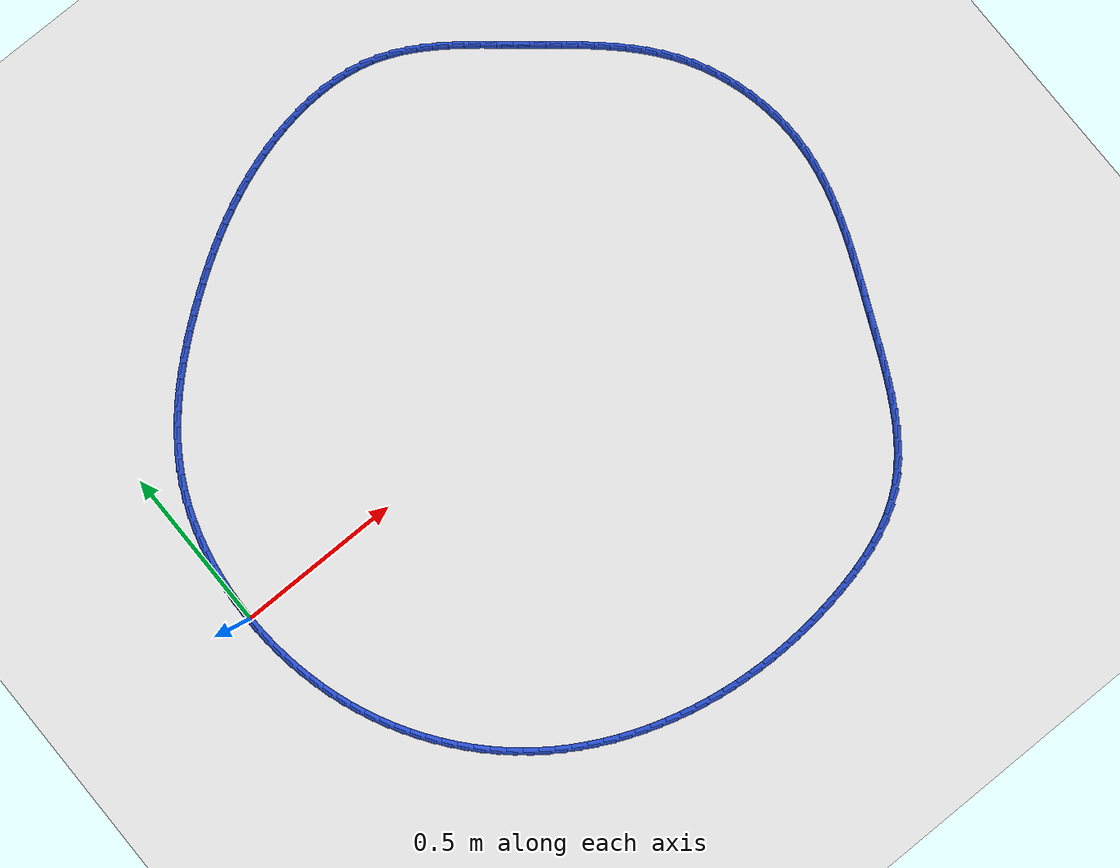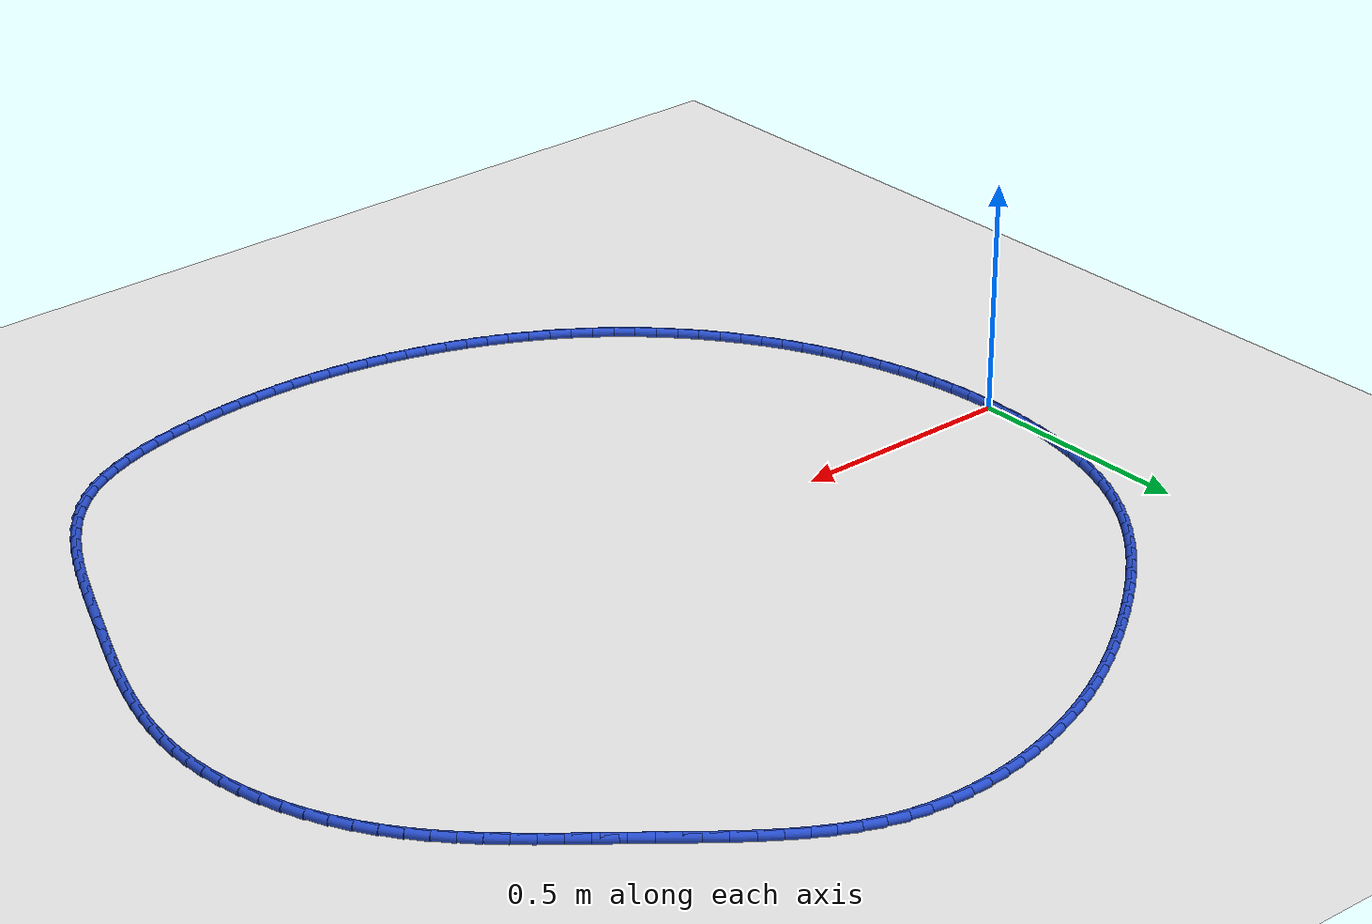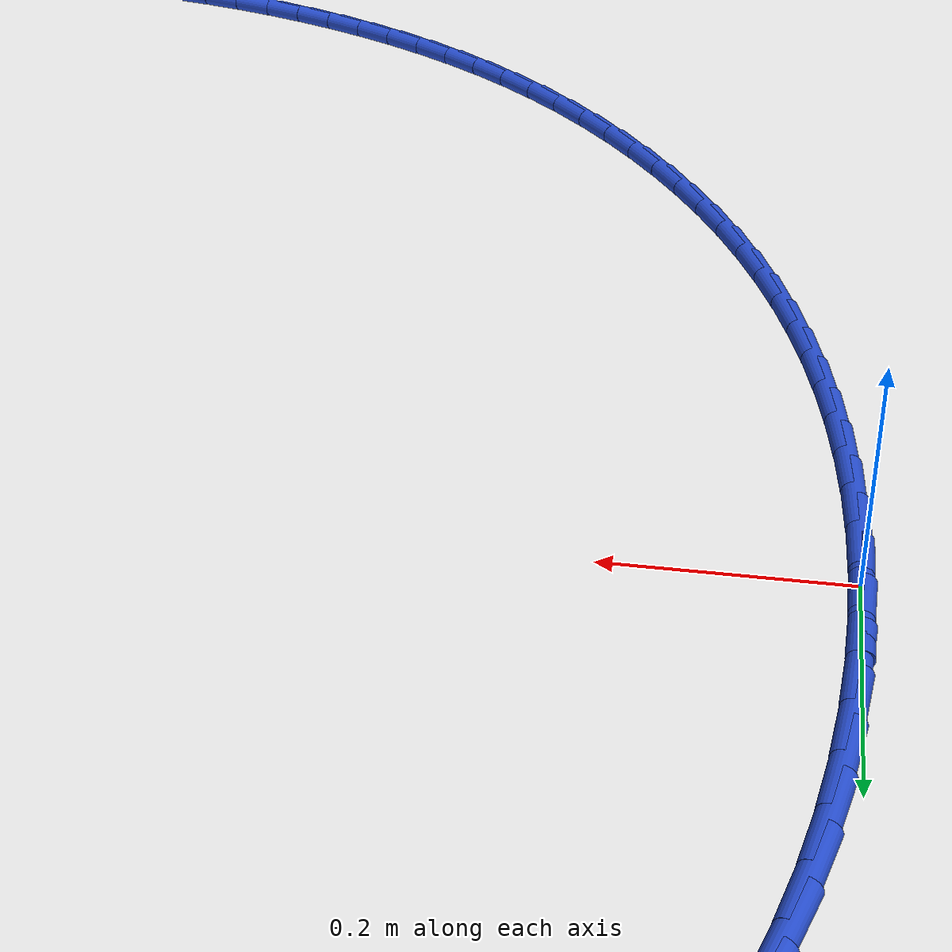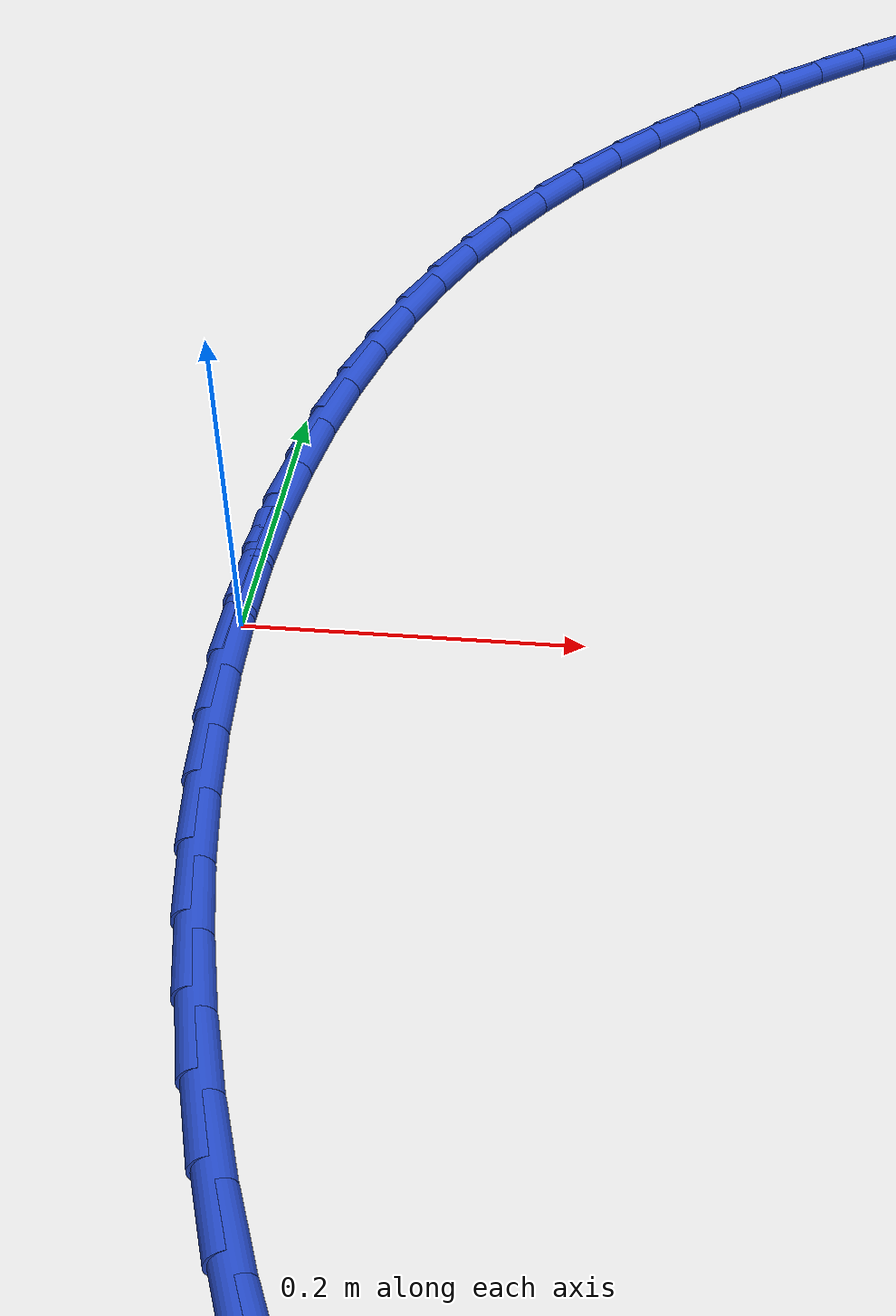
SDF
<sdf version="1.6">
 <world name="default">
  <light name="sun" type="directional">
   <pose>0 0 10 0 -0 0</pose>
   <diffuse>0.8 0.8 0.8 1</diffuse>
   <specular>0.2 0.2 0.2 1</specular>
   <attenuation>
    <range>1000</range>
    <constant>0.9</constant>
    <linear>0.01</linear>
    <quadratic>0.001</quadratic>
   </attenuation>
   <direction>-0.5 0.1 -0.9</direction>
  </light>
  <model name="ground_plane">
   <static>1</static>
   <link name="link">
    <collision name="collision">
     <geometry><plane><normal>0 0 1</normal><size>100 100</size></plane></geometry>
     <surface><friction><ode><mu>100</mu><mu2>50</mu2></ode></friction></surface>
    </collision>
    <visual name="visual">
     <cast_shadows>0</cast_shadows>
     <geometry><plane><normal>0 0 1</normal><size>100 100</size></plane></geometry>
     <material>
      <script><uri>file://media/materials/scripts/gazebo.material</uri><name>Gazebo/WhiteGlow</name></script>
     </material>
    </visual>
   </link>
  </model>
  <gravity>0 0 -9.8</gravity>
  <magnetic_field>6e-06 2.3e-05 -4.2e-05</magnetic_field>
  <atmosphere type="adiabatic"/>
  <physics name="default_physics" default="0" type="ode">
   <max_step_size>0.001</max_step_size>
   <real_time_factor>1</real_time_factor>
   <real_time_update_rate>1000</real_time_update_rate>
  </physics>
  <scene><ambient>0.4 0.4 0.4 1</ambient><background>0.7 0.7 0.7 1</background><shadows>1</shadows></scene>
  <spherical_coordinates>
   <surface_model>EARTH_WGS84</surface_model>
   <latitude_deg>0</latitude_deg>
   <longitude_deg>0</longitude_deg>
   <elevation>0</elevation>
   <heading_deg>0</heading_deg>
  </spherical_coordinates>
  <model name="line">
   <link name="link_0">
    <pose>6.765421556309548e-17 2.7755575615628914e-17 0.01 0 1.57 1.5584884787986761</pose>
    <collision name="collision">
     <geometry><cylinder><radius>0.01</radius><length>0.08</length></cylinder></geometry>
    </collision>
    <visual name="visual">
     <material>
      <script><name>Gazebo/Blue</name><uri>file://media/materials/scripts/gazebo.material</uri></script>
     </material>
     <geometry><cylinder><radius>0.01</radius><length>0.08</length></cylinder></geometry>
    </visual>
   </link>
   <link name="link_1">
    <pose>0.0005716995542776566 0.046447655719377944 0.01 0 1.57 1.514196573088559</pose>
    <collision name="collision">
     <geometry><cylinder><radius>0.01</radius><length>0.08</length></cylinder></geometry>
    </collision>
    <visual name="visual">
     <material>
      <script><name>Gazebo/Blue</name><uri>file://media/materials/scripts/gazebo.material</uri></script>
     </material>
     <geometry><cylinder><radius>0.01</radius><length>0.08</length></cylinder></geometry>
    </visual>
   </link>
   <link name="link_2">
    <pose>0.0032023153459476506 0.0928755274340366 0.01 0 1.57 1.4686242328260348</pose>
    <collision name="collision">
     <geometry><cylinder><radius>0.01</radius><length>0.08</length></cylinder></geometry>
    </collision>
    <visual name="visual">
     <material>
      <script><name>Gazebo/Blue</name><uri>file://media/materials/scripts/gazebo.material</uri></script>
     </material>
     <geometry><cylinder><radius>0.01</radius><length>0.08</length></cylinder></geometry>
    </visual>
   </link>
   <link name="link_3">
    <pose>0.00794377737591002 0.1391205580400249 0.01 0 1.57 1.4214937126309368</pose>
    <collision name="collision">
     <geometry><cylinder><radius>0.01</radius><length>0.08</length></cylinder></geometry>
    </collision>
    <visual name="visual">
     <material>
      <script><name>Gazebo/Blue</name><uri>file://media/materials/scripts/gazebo.material</uri></script>
     </material>
     <geometry><cylinder><radius>0.01</radius><length>0.08</length></cylinder></geometry>
    </visual>
   </link>
   <link name="link_4">
    <pose>0.01484801564506474 0.18501969043339178 0.01 0 1.57 1.3725343054478156</pose>
    <collision name="collision">
     <geometry><cylinder><radius>0.01</radius><length>0.08</length></cylinder></geometry>
    </collision>
    <visual name="visual">
     <material>
      <script><name>Gazebo/Blue</name><uri>file://media/materials/scripts/gazebo.material</uri></script>
     </material>
     <geometry><cylinder><radius>0.01</radius><length>0.08</length></cylinder></geometry>
    </visual>
   </link>
   <link name="link_5">
    <pose>0.0239669601543118 0.2304098675101861 0.01 0 1.57 1.3214859028333439</pose>
    <collision name="collision">
     <geometry><cylinder><radius>0.01</radius><length>0.08</length></cylinder></geometry>
    </collision>
    <visual name="visual">
     <material>
      <script><name>Gazebo/Blue</name><uri>file://media/materials/scripts/gazebo.material</uri></script>
     </material>
     <geometry><cylinder><radius>0.01</radius><length>0.08</length></cylinder></geometry>
    </visual>
   </link>
   <link name="link_6">
    <pose>0.03535254090455118 0.27512803216645687 0.01 0 1.57 1.2681049622585925</pose>
    <collision name="collision">
     <geometry><cylinder><radius>0.01</radius><length>0.08</length></cylinder></geometry>
    </collision>
    <visual name="visual">
     <material>
      <script><name>Gazebo/Blue</name><uri>file://media/materials/scripts/gazebo.material</uri></script>
     </material>
     <geometry><cylinder><radius>0.01</radius><length>0.08</length></cylinder></geometry>
    </visual>
   </link>
   <link name="link_7">
    <pose>0.049056687896682855 0.31901112729825304 0.01 0 1.57 1.2121732647211978</pose>
    <collision name="collision">
     <geometry><cylinder><radius>0.01</radius><length>0.08</length></cylinder></geometry>
    </collision>
    <visual name="visual">
     <material>
      <script><name>Gazebo/Blue</name><uri>file://media/materials/scripts/gazebo.material</uri></script>
     </material>
     <geometry><cylinder><radius>0.01</radius><length>0.08</length></cylinder></geometry>
    </visual>
   </link>
   <link name="link_8">
    <pose>0.0651313311316068 0.36189609580162335 0.01 0 1.57 1.1535097312707923</pose>
    <collision name="collision">
     <geometry><cylinder><radius>0.01</radius><length>0.08</length></cylinder></geometry>
    </collision>
    <visual name="visual">
     <material>
      <script><name>Gazebo/Blue</name><uri>file://media/materials/scripts/gazebo.material</uri></script>
     </material>
     <geometry><cylinder><radius>0.01</radius><length>0.08</length></cylinder></geometry>
    </visual>
   </link>
   <link name="link_9">
    <pose>0.08362840061022302 0.403619880572617 0.01 0 1.57 1.0920042835123835</pose>
    <collision name="collision">
     <geometry><cylinder><radius>0.01</radius><length>0.08</length></cylinder></geometry>
    </collision>
    <visual name="visual">
     <material>
      <script><name>Gazebo/Blue</name><uri>file://media/materials/scripts/gazebo.material</uri></script>
     </material>
     <geometry><cylinder><radius>0.01</radius><length>0.08</length></cylinder></geometry>
    </visual>
   </link>
   <link name="link_10">
    <pose>0.10459915249809948 0.4440200023535437 0.01 0 1.57 1.0298332348828487</pose>
    <collision name="collision">
     <geometry><cylinder><radius>0.01</radius><length>0.08</length></cylinder></geometry>
    </collision>
    <visual name="visual">
     <material>
      <script><name>Gazebo/Blue</name><uri>file://media/materials/scripts/gazebo.material</uri></script>
     </material>
     <geometry><cylinder><radius>0.01</radius><length>0.08</length></cylinder></geometry>
    </visual>
   </link>
   <link name="link_11">
    <pose>0.12801661715924728 0.48300106428027234 0.01 0 1.57 0.9714010375299906</pose>
    <collision name="collision">
     <geometry><cylinder><radius>0.01</radius><length>0.08</length></cylinder></geometry>
    </collision>
    <visual name="visual">
     <material>
      <script><name>Gazebo/Blue</name><uri>file://media/materials/scripts/gazebo.material</uri></script>
     </material>
     <geometry><cylinder><radius>0.01</radius><length>0.08</length></cylinder></geometry>
    </visual>
   </link>
   <link name="link_12">
    <pose>0.15370364644644152 0.5205964547972824 0.01 0 1.57 0.9173242000535418</pose>
    <collision name="collision">
     <geometry><cylinder><radius>0.01</radius><length>0.08</length></cylinder></geometry>
    </collision>
    <visual name="visual">
     <material>
      <script><name>Gazebo/Blue</name><uri>file://media/materials/scripts/gazebo.material</uri></script>
     </material>
     <geometry><cylinder><radius>0.01</radius><length>0.08</length></cylinder></geometry>
    </visual>
   </link>
   <link name="link_13">
    <pose>0.18146607908762974 0.5568541519232436 0.01 0 1.57 0.8676171396973472</pose>
    <collision name="collision">
     <geometry><cylinder><radius>0.01</radius><length>0.08</length></cylinder></geometry>
    </collision>
    <visual name="visual">
     <material>
      <script><name>Gazebo/Blue</name><uri>file://media/materials/scripts/gazebo.material</uri></script>
     </material>
     <geometry><cylinder><radius>0.01</radius><length>0.08</length></cylinder></geometry>
    </visual>
   </link>
   <link name="link_14">
    <pose>0.21110975381075933 0.5918221336768252 0.01 0 1.57 0.8222029213232607</pose>
    <collision name="collision">
     <geometry><cylinder><radius>0.01</radius><length>0.08</length></cylinder></geometry>
    </collision>
    <visual name="visual">
     <material>
      <script><name>Gazebo/Blue</name><uri>file://media/materials/scripts/gazebo.material</uri></script>
     </material>
     <geometry><cylinder><radius>0.01</radius><length>0.08</length></cylinder></geometry>
    </visual>
   </link>
   <link name="link_15">
    <pose>0.2424405093437778 0.6255483780766966 0.01 0 1.57 0.7809427596734648</pose>
    <collision name="collision">
     <geometry><cylinder><radius>0.01</radius><length>0.08</length></cylinder></geometry>
    </collision>
    <visual name="visual">
     <material>
      <script><name>Gazebo/Blue</name><uri>file://media/materials/scripts/gazebo.material</uri></script>
     </material>
     <geometry><cylinder><radius>0.01</radius><length>0.08</length></cylinder></geometry>
    </visual>
   </link>
   <link name="link_16">
    <pose>0.27526418441463263 0.6580808631415275 0.01 0 1.57 0.7436613765094798</pose>
    <collision name="collision">
     <geometry><cylinder><radius>0.01</radius><length>0.08</length></cylinder></geometry>
    </collision>
    <visual name="visual">
     <material>
      <script><name>Gazebo/Blue</name><uri>file://media/materials/scripts/gazebo.material</uri></script>
     </material>
     <geometry><cylinder><radius>0.01</radius><length>0.08</length></cylinder></geometry>
    </visual>
   </link>
   <link name="link_17">
    <pose>0.309386617751271 0.6894675668899863 0.01 0 1.57 0.710167448398299</pose>
    <collision name="collision">
     <geometry><cylinder><radius>0.01</radius><length>0.08</length></cylinder></geometry>
    </collision>
    <visual name="visual">
     <material>
      <script><name>Gazebo/Blue</name><uri>file://media/materials/scripts/gazebo.material</uri></script>
     </material>
     <geometry><cylinder><radius>0.01</radius><length>0.08</length></cylinder></geometry>
    </visual>
   </link>
   <link name="link_18">
    <pose>0.34461364808164086 0.7197564673407438 0.01 0 1.57 0.6802693483953398</pose>
    <collision name="collision">
     <geometry><cylinder><radius>0.01</radius><length>0.08</length></cylinder></geometry>
    </collision>
    <visual name="visual">
     <material>
      <script><name>Gazebo/Blue</name><uri>file://media/materials/scripts/gazebo.material</uri></script>
     </material>
     <geometry><cylinder><radius>0.01</radius><length>0.08</length></cylinder></geometry>
    </visual>
   </link>
   <link name="link_19">
    <pose>0.38075111413368906 0.7489955425124685 0.01 0 1.57 0.6537868988125435</pose>
    <collision name="collision">
     <geometry><cylinder><radius>0.01</radius><length>0.08</length></cylinder></geometry>
    </collision>
    <visual name="visual">
     <material>
      <script><name>Gazebo/Blue</name><uri>file://media/materials/scripts/gazebo.material</uri></script>
     </material>
     <geometry><cylinder><radius>0.01</radius><length>0.08</length></cylinder></geometry>
    </visual>
   </link>
   <link name="link_20">
    <pose>0.4176048546353637 0.77723277042383 0.01 0 1.57 0.6305543245731808</pose>
    <collision name="collision">
     <geometry><cylinder><radius>0.01</radius><length>0.08</length></cylinder></geometry>
    </collision>
    <visual name="visual">
     <material>
      <script><name>Gazebo/Blue</name><uri>file://media/materials/scripts/gazebo.material</uri></script>
     </material>
     <geometry><cylinder><radius>0.01</radius><length>0.08</length></cylinder></geometry>
    </visual>
   </link>
   <link name="link_21">
    <pose>0.45498097439960244 0.8045159953283338 0.01 0 1.57 0.6088742742741762</pose>
    <collision name="collision">
     <geometry><cylinder><radius>0.01</radius><length>0.08</length></cylinder></geometry>
    </collision>
    <visual name="visual">
     <material>
      <script><name>Gazebo/Blue</name><uri>file://media/materials/scripts/gazebo.material</uri></script>
     </material>
     <geometry><cylinder><radius>0.01</radius><length>0.08</length></cylinder></geometry>
    </visual>
   </link>
   <link name="link_22">
    <pose>0.49275869448761056 0.8308563047766697 0.01 0 1.57 0.5850038427479485</pose>
    <collision name="collision">
     <geometry><cylinder><radius>0.01</radius><length>0.08</length></cylinder></geometry>
    </collision>
    <visual name="visual">
     <material>
      <script><name>Gazebo/Blue</name><uri>file://media/materials/scripts/gazebo.material</uri></script>
     </material>
     <geometry><cylinder><radius>0.01</radius><length>0.08</length></cylinder></geometry>
    </visual>
   </link>
   <link name="link_23">
    <pose>0.5309894540610389 0.8561782095368335 0.01 0 1.57 0.558423854053083</pose>
    <collision name="collision">
     <geometry><cylinder><radius>0.01</radius><length>0.08</length></cylinder></geometry>
    </collision>
    <visual name="visual">
     <material>
      <script><name>Gazebo/Blue</name><uri>file://media/materials/scripts/gazebo.material</uri></script>
     </material>
     <geometry><cylinder><radius>0.01</radius><length>0.08</length></cylinder></geometry>
    </visual>
   </link>
   <link name="link_24">
    <pose>0.5697494710328551 0.8803937637037849 0.01 0 1.57 0.5291740657783479</pose>
    <collision name="collision">
     <geometry><cylinder><radius>0.01</radius><length>0.08</length></cylinder></geometry>
    </collision>
    <visual name="visual">
     <material>
      <script><name>Gazebo/Blue</name><uri>file://media/materials/scripts/gazebo.material</uri></script>
     </material>
     <geometry><cylinder><radius>0.01</radius><length>0.08</length></cylinder></geometry>
    </visual>
   </link>
   <link name="link_25">
    <pose>0.6091149633160268 0.9034150213724829 0.01 0 1.57 0.4973256388814062</pose>
    <collision name="collision">
     <geometry><cylinder><radius>0.01</radius><length>0.08</length></cylinder></geometry>
    </collision>
    <visual name="visual">
     <material>
      <script><name>Gazebo/Blue</name><uri>file://media/materials/scripts/gazebo.material</uri></script>
     </material>
     <geometry><cylinder><radius>0.01</radius><length>0.08</length></cylinder></geometry>
    </visual>
   </link>
   <link name="link_26">
    <pose>0.6491621488235214 0.9251540366378873 0.01 0 1.57 0.46298626982880187</pose>
    <collision name="collision">
     <geometry><cylinder><radius>0.01</radius><length>0.08</length></cylinder></geometry>
    </collision>
    <visual name="visual">
     <material>
      <script><name>Gazebo/Blue</name><uri>file://media/materials/scripts/gazebo.material</uri></script>
     </material>
     <geometry><cylinder><radius>0.01</radius><length>0.08</length></cylinder></geometry>
    </visual>
   </link>
   <link name="link_27">
    <pose>0.6899672454683065 0.9455228635949577 0.01 0 1.57 0.42630445086969593</pose>
    <collision name="collision">
     <geometry><cylinder><radius>0.01</radius><length>0.08</length></cylinder></geometry>
    </collision>
    <visual name="visual">
     <material>
      <script><name>Gazebo/Blue</name><uri>file://media/materials/scripts/gazebo.material</uri></script>
     </material>
     <geometry><cylinder><radius>0.01</radius><length>0.08</length></cylinder></geometry>
    </visual>
   </link>
   <link name="link_28">
    <pose>0.7316064711633496 0.9644335563386531 0.01 0 1.57 0.38747223377658824</pose>
    <collision name="collision">
     <geometry><cylinder><radius>0.01</radius><length>0.08</length></cylinder></geometry>
    </collision>
    <visual name="visual">
     <material>
      <script><name>Gazebo/Blue</name><uri>file://media/materials/scripts/gazebo.material</uri></script>
     </material>
     <geometry><cylinder><radius>0.01</radius><length>0.08</length></cylinder></geometry>
    </visual>
   </link>
   <link name="link_29">
    <pose>0.7741560438216187 0.9817981689639338 0.01 0 1.57 0.3467258663415571</pose>
    <collision name="collision">
     <geometry><cylinder><radius>0.01</radius><length>0.08</length></cylinder></geometry>
    </collision>
    <visual name="visual">
     <material>
      <script><name>Gazebo/Blue</name><uri>file://media/materials/scripts/gazebo.material</uri></script>
     </material>
     <geometry><cylinder><radius>0.01</radius><length>0.08</length></cylinder></geometry>
    </visual>
   </link>
   <link name="link_30">
    <pose>0.817692181356081 0.9975287555657586 0.01 0 1.57 0.3043151685032217</pose>
    <collision name="collision">
     <geometry><cylinder><radius>0.01</radius><length>0.08</length></cylinder></geometry>
    </collision>
    <visual name="visual">
     <material>
      <script><name>Gazebo/Blue</name><uri>file://media/materials/scripts/gazebo.material</uri></script>
     </material>
     <geometry><cylinder><radius>0.01</radius><length>0.08</length></cylinder></geometry>
    </visual>
   </link>
   <link name="link_31">
    <pose>0.8622772089891256 1.0115316055564987 0.01 0 1.57 0.25993792252258</pose>
    <collision name="collision">
     <geometry><cylinder><radius>0.01</radius><length>0.08</length></cylinder></geometry>
    </collision>
    <visual name="visual">
     <material>
      <script><name>Gazebo/Blue</name><uri>file://media/materials/scripts/gazebo.material</uri></script>
     </material>
     <geometry><cylinder><radius>0.01</radius><length>0.08</length></cylinder></geometry>
    </visual>
   </link>
   <link name="link_32">
    <pose>0.9077838051237057 1.0236343156207328 0.01 0 1.57 0.21277090962695178</pose>
    <collision name="collision">
     <geometry><cylinder><radius>0.01</radius><length>0.08</length></cylinder></geometry>
    </collision>
    <visual name="visual">
     <material>
      <script><name>Gazebo/Blue</name><uri>file://media/materials/scripts/gazebo.material</uri></script>
     </material>
     <geometry><cylinder><radius>0.01</radius><length>0.08</length></cylinder></geometry>
    </visual>
   </link>
   <link name="link_33">
    <pose>0.9539474529796185 1.0336075541843197 0.01 0 1.57 0.16210223971566706</pose>
    <collision name="collision">
     <geometry><cylinder><radius>0.01</radius><length>0.08</length></cylinder></geometry>
    </collision>
    <visual name="visual">
     <material>
      <script><name>Gazebo/Blue</name><uri>file://media/materials/scripts/gazebo.material</uri></script>
     </material>
     <geometry><cylinder><radius>0.01</radius><length>0.08</length></cylinder></geometry>
    </visual>
   </link>
   <link name="link_34">
    <pose>1.0005005793275596 1.041220721419223 0.01 0 1.57 0.10719316870362879</pose>
    <collision name="collision">
     <geometry><cylinder><radius>0.01</radius><length>0.08</length></cylinder></geometry>
    </collision>
    <visual name="visual">
     <material>
      <script><name>Gazebo/Blue</name><uri>file://media/materials/scripts/gazebo.material</uri></script>
     </material>
     <geometry><cylinder><radius>0.01</radius><length>0.08</length></cylinder></geometry>
    </visual>
   </link>
   <link name="link_35">
    <pose>1.0471756109382253 1.0462432174974072 0.01 0 1.57 0.0472730541252099</pose>
    <collision name="collision">
     <geometry><cylinder><radius>0.01</radius><length>0.08</length></cylinder></geometry>
    </collision>
    <visual name="visual">
     <material>
      <script><name>Gazebo/Blue</name><uri>file://media/materials/scripts/gazebo.material</uri></script>
     </material>
     <geometry><cylinder><radius>0.01</radius><length>0.08</length></cylinder></geometry>
    </visual>
   </link>
   <link name="link_36">
    <pose>1.0937049745823109 1.048444442590838 0.01 0 1.57 -0.018443642220635454</pose>
    <collision name="collision">
     <geometry><cylinder><radius>0.01</radius><length>0.08</length></cylinder></geometry>
    </collision>
    <visual name="visual">
     <material>
      <script><name>Gazebo/Blue</name><uri>file://media/materials/scripts/gazebo.material</uri></script>
     </material>
     <geometry><cylinder><radius>0.01</radius><length>0.08</length></cylinder></geometry>
    </visual>
   </link>
   <link name="link_37">
    <pose>1.1398210970305143 1.0475937968714792 0.01 0 1.57 -0.09071738016088018</pose>
    <collision name="collision">
     <geometry><cylinder><radius>0.01</radius><length>0.08</length></cylinder></geometry>
    </collision>
    <visual name="visual">
     <material>
      <script><name>Gazebo/Blue</name><uri>file://media/materials/scripts/gazebo.material</uri></script>
     </material>
     <geometry><cylinder><radius>0.01</radius><length>0.08</length></cylinder></geometry>
    </visual>
   </link>
   <link name="link_38">
    <pose>1.185256405053529 1.0434606805112954 0.01 0 1.57 -0.17021186831532467</pose>
    <collision name="collision">
     <geometry><cylinder><radius>0.01</radius><length>0.08</length></cylinder></geometry>
    </collision>
    <visual name="visual">
     <material>
      <script><name>Gazebo/Blue</name><uri>file://media/materials/scripts/gazebo.material</uri></script>
     </material>
     <geometry><cylinder><radius>0.01</radius><length>0.08</length></cylinder></geometry>
    </visual>
   </link>
   <link name="link_39">
    <pose>1.2297433254220531 1.0358144936822513 0.01 0 1.57 -0.25738226622226457</pose>
    <collision name="collision">
     <geometry><cylinder><radius>0.01</radius><length>0.08</length></cylinder></geometry>
    </collision>
    <visual name="visual">
     <material>
      <script><name>Gazebo/Blue</name><uri>file://media/materials/scripts/gazebo.material</uri></script>
     </material>
     <geometry><cylinder><radius>0.01</radius><length>0.08</length></cylinder></geometry>
    </visual>
   </link>
   <link name="link_40">
    <pose>1.2730143138525405 1.0244246823964231 0.01 0 1.57 -0.3486361929021818</pose>
    <collision name="collision">
     <geometry><cylinder><radius>0.01</radius><length>0.08</length></cylinder></geometry>
    </collision>
    <visual name="visual">
     <material>
      <script><name>Gazebo/Blue</name><uri>file://media/materials/scripts/gazebo.material</uri></script>
     </material>
     <geometry><cylinder><radius>0.01</radius><length>0.08</length></cylinder></geometry>
    </visual>
   </link>
   <link name="link_41">
    <pose>1.3148916546373968 1.0092029501883182 0.01 0 1.57 -0.431375019111803</pose>
    <collision name="collision">
     <geometry><cylinder><radius>0.01</radius><length>0.08</length></cylinder></geometry>
    </collision>
    <visual name="visual">
     <material>
      <script><name>Gazebo/Blue</name><uri>file://media/materials/scripts/gazebo.material</uri></script>
     </material>
     <geometry><cylinder><radius>0.01</radius><length>0.08</length></cylinder></geometry>
    </visual>
   </link>
   <link name="link_42">
    <pose>1.3554861237072704 0.990517871975126 0.01 0 1.57 -0.5023417541619757</pose>
    <collision name="collision">
     <geometry><cylinder><radius>0.01</radius><length>0.08</length></cylinder></geometry>
    </collision>
    <visual name="visual">
     <material>
      <script><name>Gazebo/Blue</name><uri>file://media/materials/scripts/gazebo.material</uri></script>
     </material>
     <geometry><cylinder><radius>0.01</radius><length>0.08</length></cylinder></geometry>
    </visual>
   </link>
   <link name="link_43">
    <pose>1.3949662960409819 0.9688295564571869 0.01 0 1.57 -0.5613454890477821</pose>
    <collision name="collision">
     <geometry><cylinder><radius>0.01</radius><length>0.08</length></cylinder></geometry>
    </collision>
    <visual name="visual">
     <material>
      <script><name>Gazebo/Blue</name><uri>file://media/materials/scripts/gazebo.material</uri></script>
     </material>
     <geometry><cylinder><radius>0.01</radius><length>0.08</length></cylinder></geometry>
    </visual>
   </link>
   <link name="link_44">
    <pose>1.4335007466173528 0.9445981123348415 0.01 0 1.57 -0.6086673356558895</pose>
    <collision name="collision">
     <geometry><cylinder><radius>0.01</radius><length>0.08</length></cylinder></geometry>
    </collision>
    <visual name="visual">
     <material>
      <script><name>Gazebo/Blue</name><uri>file://media/materials/scripts/gazebo.material</uri></script>
     </material>
     <geometry><cylinder><radius>0.01</radius><length>0.08</length></cylinder></geometry>
    </visual>
   </link>
   <link name="link_45">
    <pose>1.4712580504152033 0.9182836483084309 0.01 0 1.57 -0.6448061670911457</pose>
    <collision name="collision">
     <geometry><cylinder><radius>0.01</radius><length>0.08</length></cylinder></geometry>
    </collision>
    <visual name="visual">
     <material>
      <script><name>Gazebo/Blue</name><uri>file://media/materials/scripts/gazebo.material</uri></script>
     </material>
     <geometry><cylinder><radius>0.01</radius><length>0.08</length></cylinder></geometry>
    </visual>
   </link>
   <link name="link_46">
    <pose>1.5084067824133554 0.8903462730782957 0.01 0 1.57 -0.6702933069164778</pose>
    <collision name="collision">
     <geometry><cylinder><radius>0.01</radius><length>0.08</length></cylinder></geometry>
    </collision>
    <visual name="visual">
     <material>
      <script><name>Gazebo/Blue</name><uri>file://media/materials/scripts/gazebo.material</uri></script>
     </material>
     <geometry><cylinder><radius>0.01</radius><length>0.08</length></cylinder></geometry>
    </visual>
   </link>
   <link name="link_47">
    <pose>1.5451155175906277 0.8612460953447763 0.01 0 1.57 -0.6855737150019687</pose>
    <collision name="collision">
     <geometry><cylinder><radius>0.01</radius><length>0.08</length></cylinder></geometry>
    </collision>
    <visual name="visual">
     <material>
      <script><name>Gazebo/Blue</name><uri>file://media/materials/scripts/gazebo.material</uri></script>
     </material>
     <geometry><cylinder><radius>0.01</radius><length>0.08</length></cylinder></geometry>
    </visual>
   </link>
   <link name="link_48">
    <pose>1.5815528309258429 0.8314432238082134 0.01 0 1.57 -0.6909374716187453</pose>
    <collision name="collision">
     <geometry><cylinder><radius>0.01</radius><length>0.08</length></cylinder></geometry>
    </collision>
    <visual name="visual">
     <material>
      <script><name>Gazebo/Blue</name><uri>file://media/materials/scripts/gazebo.material</uri></script>
     </material>
     <geometry><cylinder><radius>0.01</radius><length>0.08</length></cylinder></geometry>
    </visual>
   </link>
   <link name="link_49">
    <pose>1.617887297397821 0.8013977671689481 0.01 0 1.57 -0.6870441762420141</pose>
    <collision name="collision">
     <geometry><cylinder><radius>0.01</radius><length>0.08</length></cylinder></geometry>
    </collision>
    <visual name="visual">
     <material>
      <script><name>Gazebo/Blue</name><uri>file://media/materials/scripts/gazebo.material</uri></script>
     </material>
     <geometry><cylinder><radius>0.01</radius><length>0.08</length></cylinder></geometry>
    </visual>
   </link>
   <link name="link_50">
    <pose>1.654273696653284 0.7715471324895404 0.01 0 1.57 -0.6830043097853576</pose>
    <collision name="collision">
     <geometry><cylinder><radius>0.01</radius><length>0.08</length></cylinder></geometry>
    </collision>
    <visual name="visual">
     <material>
      <script><name>Gazebo/Blue</name><uri>file://media/materials/scripts/gazebo.material</uri></script>
     </material>
     <geometry><cylinder><radius>0.01</radius><length>0.08</length></cylinder></geometry>
    </visual>
   </link>
   <link name="link_51">
    <pose>1.6906410064363233 0.741957146578663 0.01 0 1.57 -0.6863307857866872</pose>
    <collision name="collision">
     <geometry><cylinder><radius>0.01</radius><length>0.08</length></cylinder></geometry>
    </collision>
    <visual name="visual">
     <material>
      <script><name>Gazebo/Blue</name><uri>file://media/materials/scripts/gazebo.material</uri></script>
     </material>
     <geometry><cylinder><radius>0.01</radius><length>0.08</length></cylinder></geometry>
    </visual>
   </link>
   <link name="link_52">
    <pose>1.7267339023714163 0.7123903481521966 0.01 0 1.57 -0.6973625935732917</pose>
    <collision name="collision">
     <geometry><cylinder><radius>0.01</radius><length>0.08</length></cylinder></geometry>
    </collision>
    <visual name="visual">
     <material>
      <script><name>Gazebo/Blue</name><uri>file://media/materials/scripts/gazebo.material</uri></script>
     </material>
     <geometry><cylinder><radius>0.01</radius><length>0.08</length></cylinder></geometry>
    </visual>
   </link>
   <link name="link_53">
    <pose>1.7622916721609385 0.6826004095460714 0.01 0 1.57 -0.7162616468009146</pose>
    <collision name="collision">
     <geometry><cylinder><radius>0.01</radius><length>0.08</length></cylinder></geometry>
    </collision>
    <visual name="visual">
     <material>
      <script><name>Gazebo/Blue</name><uri>file://media/materials/scripts/gazebo.material</uri></script>
     </material>
     <geometry><cylinder><radius>0.01</radius><length>0.08</length></cylinder></geometry>
    </visual>
   </link>
   <link name="link_54">
    <pose>1.797053603507267 0.6523410030962175 0.01 0 1.57 -0.7432130311848203</pose>
    <collision name="collision">
     <geometry><cylinder><radius>0.01</radius><length>0.08</length></cylinder></geometry>
    </collision>
    <visual name="visual">
     <material>
      <script><name>Gazebo/Blue</name><uri>file://media/materials/scripts/gazebo.material</uri></script>
     </material>
     <geometry><cylinder><radius>0.01</radius><length>0.08</length></cylinder></geometry>
    </visual>
   </link>
   <link name="link_55">
    <pose>1.8307589841127778 0.6213658011385641 0.01 0 1.57 -0.7783902822373173</pose>
    <collision name="collision">
     <geometry><cylinder><radius>0.01</radius><length>0.08</length></cylinder></geometry>
    </collision>
    <visual name="visual">
     <material>
      <script><name>Gazebo/Blue</name><uri>file://media/materials/scripts/gazebo.material</uri></script>
     </material>
     <geometry><cylinder><radius>0.01</radius><length>0.08</length></cylinder></geometry>
    </visual>
   </link>
   <link name="link_56">
    <pose>1.8631471016798473 0.5894284760090414 0.01 0 1.57 -0.8219013723221209</pose>
    <collision name="collision">
     <geometry><cylinder><radius>0.01</radius><length>0.08</length></cylinder></geometry>
    </collision>
    <visual name="visual">
     <material>
      <script><name>Gazebo/Blue</name><uri>file://media/materials/scripts/gazebo.material</uri></script>
     </material>
     <geometry><cylinder><radius>0.01</radius><length>0.08</length></cylinder></geometry>
    </visual>
   </link>
   <link name="link_57">
    <pose>1.8939572439108514 0.5562827000435787 0.01 0 1.57 -0.8737146574781458</pose>
    <collision name="collision">
     <geometry><cylinder><radius>0.01</radius><length>0.08</length></cylinder></geometry>
    </collision>
    <visual name="visual">
     <material>
      <script><name>Gazebo/Blue</name><uri>file://media/materials/scripts/gazebo.material</uri></script>
     </material>
     <geometry><cylinder><radius>0.01</radius><length>0.08</length></cylinder></geometry>
    </visual>
   </link>
   <link name="link_58">
    <pose>1.9229286985081653 0.5216821455781061 0.01 0 1.57 -0.93356891842563</pose>
    <collision name="collision">
     <geometry><cylinder><radius>0.01</radius><length>0.08</length></cylinder></geometry>
    </collision>
    <visual name="visual">
     <material>
      <script><name>Gazebo/Blue</name><uri>file://media/materials/scripts/gazebo.material</uri></script>
     </material>
     <geometry><cylinder><radius>0.01</radius><length>0.08</length></cylinder></geometry>
    </visual>
   </link>
   <link name="link_59">
    <pose>1.9498007531741668 0.48538048494855296 0.01 0 1.57 -1.0008645993232215</pose>
    <collision name="collision">
     <geometry><cylinder><radius>0.01</radius><length>0.08</length></cylinder></geometry>
    </collision>
    <visual name="visual">
     <material>
      <script><name>Gazebo/Blue</name><uri>file://media/materials/scripts/gazebo.material</uri></script>
     </material>
     <geometry><cylinder><radius>0.01</radius><length>0.08</length></cylinder></geometry>
    </visual>
   </link>
   <link name="link_60">
    <pose>1.9743129762506522 0.44713226359350366 0.01 0 1.57 -1.0718996389974287</pose>
    <collision name="collision">
     <geometry><cylinder><radius>0.01</radius><length>0.08</length></cylinder></geometry>
    </collision>
    <visual name="visual">
     <material>
      <script><name>Gazebo/Blue</name><uri>file://media/materials/scripts/gazebo.material</uri></script>
     </material>
     <geometry><cylinder><radius>0.01</radius><length>0.08</length></cylinder></geometry>
    </visual>
   </link>
   <link name="link_61">
    <pose>1.9962578987159565 0.4068568000195855 0.01 0 1.57 -1.1405684976423738</pose>
    <collision name="collision">
     <geometry><cylinder><radius>0.01</radius><length>0.08</length></cylinder></geometry>
    </collision>
    <visual name="visual">
     <material>
      <script><name>Gazebo/Blue</name><uri>file://media/materials/scripts/gazebo.material</uri></script>
     </material>
     <geometry><cylinder><radius>0.01</radius><length>0.08</length></cylinder></geometry>
    </visual>
   </link>
   <link name="link_62">
    <pose>2.0155431605134826 0.36483153042874117 0.01 0 1.57 -1.2069031095545313</pose>
    <collision name="collision">
     <geometry><cylinder><radius>0.01</radius><length>0.08</length></cylinder></geometry>
    </collision>
    <visual name="visual">
     <material>
      <script><name>Gazebo/Blue</name><uri>file://media/materials/scripts/gazebo.material</uri></script>
     </material>
     <geometry><cylinder><radius>0.01</radius><length>0.08</length></cylinder></geometry>
    </visual>
   </link>
   <link name="link_63">
    <pose>2.0320915134600224 0.32138090586025686 0.01 0 1.57 -1.2717636793128944</pose>
    <collision name="collision">
     <geometry><cylinder><radius>0.01</radius><length>0.08</length></cylinder></geometry>
    </collision>
    <visual name="visual">
     <material>
      <script><name>Gazebo/Blue</name><uri>file://media/materials/scripts/gazebo.material</uri></script>
     </material>
     <geometry><cylinder><radius>0.01</radius><length>0.08</length></cylinder></geometry>
    </visual>
   </link>
   <link name="link_64">
    <pose>2.045825709372368 0.2768293773534201 0.01 0 1.57 -1.3360008692846639</pose>
    <collision name="collision">
     <geometry><cylinder><radius>0.01</radius><length>0.08</length></cylinder></geometry>
    </collision>
    <visual name="visual">
     <material>
      <script><name>Gazebo/Blue</name><uri>file://media/materials/scripts/gazebo.material</uri></script>
     </material>
     <geometry><cylinder><radius>0.01</radius><length>0.08</length></cylinder></geometry>
    </visual>
   </link>
   <link name="link_65">
    <pose>2.056668500067312 0.23150139594751754 0.01 0 1.57 -1.400463411373081</pose>
    <collision name="collision">
     <geometry><cylinder><radius>0.01</radius><length>0.08</length></cylinder></geometry>
    </collision>
    <visual name="visual">
     <material>
      <script><name>Gazebo/Blue</name><uri>file://media/materials/scripts/gazebo.material</uri></script>
     </material>
     <geometry><cylinder><radius>0.01</radius><length>0.08</length></cylinder></geometry>
    </visual>
   </link>
   <link name="link_66">
    <pose>2.064542637361646 0.18572141268183545 0.01 0 1.57 -1.4660085021436622</pose>
    <collision name="collision">
     <geometry><cylinder><radius>0.01</radius><length>0.08</length></cylinder></geometry>
    </collision>
    <visual name="visual">
     <material>
      <script><name>Gazebo/Blue</name><uri>file://media/materials/scripts/gazebo.material</uri></script>
     </material>
     <geometry><cylinder><radius>0.01</radius><length>0.08</length></cylinder></geometry>
    </visual>
   </link>
   <link name="link_67">
    <pose>2.0693708730721627 0.1398138785956615 0.01 0 1.57 -1.5335118783204629</pose>
    <collision name="collision">
     <geometry><cylinder><radius>0.01</radius><length>0.08</length></cylinder></geometry>
    </collision>
    <visual name="visual">
     <material>
      <script><name>Gazebo/Blue</name><uri>file://media/materials/scripts/gazebo.material</uri></script>
     </material>
     <geometry><cylinder><radius>0.01</radius><length>0.08</length></cylinder></geometry>
    </visual>
   </link>
   <link name="link_68">
    <pose>2.0710759590156536 0.09410324472828174 0.01 0 1.57 1.5384218881127307</pose>
    <collision name="collision">
     <geometry><cylinder><radius>0.01</radius><length>0.08</length></cylinder></geometry>
    </collision>
    <visual name="visual">
     <material>
      <script><name>Gazebo/Blue</name><uri>file://media/materials/scripts/gazebo.material</uri></script>
     </material>
     <geometry><cylinder><radius>0.01</radius><length>0.08</length></cylinder></geometry>
    </visual>
   </link>
   <link name="link_69">
    <pose>2.0696113340067956 0.048878884416507805 0.01 0 1.57 1.471347084197816</pose>
    <collision name="collision">
     <geometry><cylinder><radius>0.01</radius><length>0.08</length></cylinder></geometry>
    </collision>
    <visual name="visual">
     <material>
      <script><name>Gazebo/Blue</name><uri>file://media/materials/scripts/gazebo.material</uri></script>
     </material>
     <geometry><cylinder><radius>0.01</radius><length>0.08</length></cylinder></geometry>
    </visual>
   </link>
   <link name="link_70">
    <pose>2.065151140202597 0.004177889356365089 0.01 0 1.57 1.4098308644106228</pose>
    <collision name="collision">
     <geometry><cylinder><radius>0.01</radius><length>0.08</length></cylinder></geometry>
    </collision>
    <visual name="visual">
     <material>
      <script><name>Gazebo/Blue</name><uri>file://media/materials/scripts/gazebo.material</uri></script>
     </material>
     <geometry><cylinder><radius>0.01</radius><length>0.08</length></cylinder></geometry>
    </visual>
   </link>
   <link name="link_71">
    <pose>2.0579661048418574 -0.040073053259532934 0.01 0 1.57 1.3545435582672212</pose>
    <collision name="collision">
     <geometry><cylinder><radius>0.01</radius><length>0.08</length></cylinder></geometry>
    </collision>
    <visual name="visual">
     <material>
      <script><name>Gazebo/Blue</name><uri>file://media/materials/scripts/gazebo.material</uri></script>
     </material>
     <geometry><cylinder><radius>0.01</radius><length>0.08</length></cylinder></geometry>
    </visual>
   </link>
   <link name="link_72">
    <pose>2.048327362897103 -0.08394772231095593 0.01 0 1.57 1.305869315369488</pose>
    <collision name="collision">
     <geometry><cylinder><radius>0.01</radius><length>0.08</length></cylinder></geometry>
    </collision>
    <visual name="visual">
     <material>
      <script><name>Gazebo/Blue</name><uri>file://media/materials/scripts/gazebo.material</uri></script>
     </material>
     <geometry><cylinder><radius>0.01</radius><length>0.08</length></cylinder></geometry>
    </visual>
   </link>
   <link name="link_73">
    <pose>2.0365060493408587 -0.12751989667767377 0.01 0 1.57 1.2639664884467154</pose>
    <collision name="collision">
     <geometry><cylinder><radius>0.01</radius><length>0.08</length></cylinder></geometry>
    </collision>
    <visual name="visual">
     <material>
      <script><name>Gazebo/Blue</name><uri>file://media/materials/scripts/gazebo.material</uri></script>
     </material>
     <geometry><cylinder><radius>0.01</radius><length>0.08</length></cylinder></geometry>
    </visual>
   </link>
   <link name="link_74">
    <pose>2.0227732991456495 -0.17086335523945428 0.01 0 1.57 1.228828698968601</pose>
    <collision name="collision">
     <geometry><cylinder><radius>0.01</radius><length>0.08</length></cylinder></geometry>
    </collision>
    <visual name="visual">
     <material>
      <script><name>Gazebo/Blue</name><uri>file://media/materials/scripts/gazebo.material</uri></script>
     </material>
     <geometry><cylinder><radius>0.01</radius><length>0.08</length></cylinder></geometry>
    </visual>
   </link>
   <link name="link_75">
    <pose>2.0074002472839996 -0.21405187687606764 0.01 0 1.57 1.2003435093777792</pose>
    <collision name="collision">
     <geometry><cylinder><radius>0.01</radius><length>0.08</length></cylinder></geometry>
    </collision>
    <visual name="visual">
     <material>
      <script><name>Gazebo/Blue</name><uri>file://media/materials/scripts/gazebo.material</uri></script>
     </material>
     <geometry><cylinder><radius>0.01</radius><length>0.08</length></cylinder></geometry>
    </visual>
   </link>
   <link name="link_76">
    <pose>1.9906580287284346 -0.2571592404672829 0.01 0 1.57 1.1783418062681639</pose>
    <collision name="collision">
     <geometry><cylinder><radius>0.01</radius><length>0.08</length></cylinder></geometry>
    </collision>
    <visual name="visual">
     <material>
      <script><name>Gazebo/Blue</name><uri>file://media/materials/scripts/gazebo.material</uri></script>
     </material>
     <geometry><cylinder><radius>0.01</radius><length>0.08</length></cylinder></geometry>
    </visual>
   </link>
   <link name="link_77">
    <pose>1.9728177784514789 -0.3002592248928695 0.01 0 1.57 1.1626354636979177</pose>
    <collision name="collision">
     <geometry><cylinder><radius>0.01</radius><length>0.08</length></cylinder></geometry>
    </collision>
    <visual name="visual">
     <material>
      <script><name>Gazebo/Blue</name><uri>file://media/materials/scripts/gazebo.material</uri></script>
     </material>
     <geometry><cylinder><radius>0.01</radius><length>0.08</length></cylinder></geometry>
    </visual>
   </link>
   <link name="link_78">
    <pose>1.9541506314256565 -0.3434256090325971 0.01 0 1.57 1.1530435955629084</pose>
    <collision name="collision">
     <geometry><cylinder><radius>0.01</radius><length>0.08</length></cylinder></geometry>
    </collision>
    <visual name="visual">
     <material>
      <script><name>Gazebo/Blue</name><uri>file://media/materials/scripts/gazebo.material</uri></script>
     </material>
     <geometry><cylinder><radius>0.01</radius><length>0.08</length></cylinder></geometry>
    </visual>
   </link>
   <link name="link_79">
    <pose>1.934927722623494 -0.3867321717662339 0.01 0 1.57 1.1494089404143863</pose>
    <collision name="collision">
     <geometry><cylinder><radius>0.01</radius><length>0.08</length></cylinder></geometry>
    </collision>
    <visual name="visual">
     <material>
      <script><name>Gazebo/Blue</name><uri>file://media/materials/scripts/gazebo.material</uri></script>
     </material>
     <geometry><cylinder><radius>0.01</radius><length>0.08</length></cylinder></geometry>
    </visual>
   </link>
   <link name="link_80">
    <pose>1.9154201870175156 -0.4302526919735499 0.01 0 1.57 1.1509368477353699</pose>
    <collision name="collision">
     <geometry><cylinder><radius>0.01</radius><length>0.08</length></cylinder></geometry>
    </collision>
    <visual name="visual">
     <material>
      <script><name>Gazebo/Blue</name><uri>file://media/materials/scripts/gazebo.material</uri></script>
     </material>
     <geometry><cylinder><radius>0.01</radius><length>0.08</length></cylinder></geometry>
    </visual>
   </link>
   <link name="link_81">
    <pose>1.895872885330871 -0.4740410566622712 0.01 0 1.57 1.1497684542478797</pose>
    <collision name="collision">
     <geometry><cylinder><radius>0.01</radius><length>0.08</length></cylinder></geometry>
    </collision>
    <visual name="visual">
     <material>
      <script><name>Gazebo/Blue</name><uri>file://media/materials/scripts/gazebo.material</uri></script>
     </material>
     <geometry><cylinder><radius>0.01</radius><length>0.08</length></cylinder></geometry>
    </visual>
   </link>
   <link name="link_82">
    <pose>1.8762240696948929 -0.5179190237014911 0.01 0 1.57 1.1408603704991176</pose>
    <collision name="collision">
     <geometry><cylinder><radius>0.01</radius><length>0.08</length></cylinder></geometry>
    </collision>
    <visual name="visual">
     <material>
      <script><name>Gazebo/Blue</name><uri>file://media/materials/scripts/gazebo.material</uri></script>
     </material>
     <geometry><cylinder><radius>0.01</radius><length>0.08</length></cylinder></geometry>
    </visual>
   </link>
   <link name="link_83">
    <pose>1.8562136230525506 -0.5615581683820703 0.01 0 1.57 1.1239894178460679</pose>
    <collision name="collision">
     <geometry><cylinder><radius>0.01</radius><length>0.08</length></cylinder></geometry>
    </collision>
    <visual name="visual">
     <material>
      <script><name>Gazebo/Blue</name><uri>file://media/materials/scripts/gazebo.material</uri></script>
     </material>
     <geometry><cylinder><radius>0.01</radius><length>0.08</length></cylinder></geometry>
    </visual>
   </link>
   <link name="link_84">
    <pose>1.8355780970699551 -0.6046275439310816 0.01 0 1.57 1.0988413681578615</pose>
    <collision name="collision">
     <geometry><cylinder><radius>0.01</radius><length>0.08</length></cylinder></geometry>
    </collision>
    <visual name="visual">
     <material>
      <script><name>Gazebo/Blue</name><uri>file://media/materials/scripts/gazebo.material</uri></script>
     </material>
     <geometry><cylinder><radius>0.01</radius><length>0.08</length></cylinder></geometry>
    </visual>
   </link>
   <link name="link_85">
    <pose>1.8140540434132193 -0.6467962035755973 0.01 0 1.57 1.0649446077537825</pose>
    <collision name="collision">
     <geometry><cylinder><radius>0.01</radius><length>0.08</length></cylinder></geometry>
    </collision>
    <visual name="visual">
     <material>
      <script><name>Gazebo/Blue</name><uri>file://media/materials/scripts/gazebo.material</uri></script>
     </material>
     <geometry><cylinder><radius>0.01</radius><length>0.08</length></cylinder></geometry>
    </visual>
   </link>
   <link name="link_86">
    <pose>1.7913780137484558 -0.6877332005426897 0.01 0 1.57 1.0217047809691011</pose>
    <collision name="collision">
     <geometry><cylinder><radius>0.01</radius><length>0.08</length></cylinder></geometry>
    </collision>
    <visual name="visual">
     <material>
      <script><name>Gazebo/Blue</name><uri>file://media/materials/scripts/gazebo.material</uri></script>
     </material>
     <geometry><cylinder><radius>0.01</radius><length>0.08</length></cylinder></geometry>
    </visual>
   </link>
   <link name="link_87">
    <pose>1.7672865597417764 -0.7271075880594318 0.01 0 1.57 0.9684681246316488</pose>
    <collision name="collision">
     <geometry><cylinder><radius>0.01</radius><length>0.08</length></cylinder></geometry>
    </collision>
    <visual name="visual">
     <material>
      <script><name>Gazebo/Blue</name><uri>file://media/materials/scripts/gazebo.material</uri></script>
     </material>
     <geometry><cylinder><radius>0.01</radius><length>0.08</length></cylinder></geometry>
    </visual>
   </link>
   <link name="link_88">
    <pose>1.7415162330592941 -0.7645884193528942 0.01 0 1.57 0.9046298813098269</pose>
    <collision name="collision">
     <geometry><cylinder><radius>0.01</radius><length>0.08</length></cylinder></geometry>
    </collision>
    <visual name="visual">
     <material>
      <script><name>Gazebo/Blue</name><uri>file://media/materials/scripts/gazebo.material</uri></script>
     </material>
     <geometry><cylinder><radius>0.01</radius><length>0.08</length></cylinder></geometry>
    </visual>
   </link>
   <link name="link_89">
    <pose>1.7138035853671214 -0.7998447476501503 0.01 0 1.57 0.8298035239855623</pose>
    <collision name="collision">
     <geometry><cylinder><radius>0.01</radius><length>0.08</length></cylinder></geometry>
    </collision>
    <visual name="visual">
     <material>
      <script><name>Gazebo/Blue</name><uri>file://media/materials/scripts/gazebo.material</uri></script>
     </material>
     <geometry><cylinder><radius>0.01</radius><length>0.08</length></cylinder></geometry>
    </visual>
   </link>
   <link name="link_90">
    <pose>1.6838851683313707 -0.832545626178272 0.01 0 1.57 0.7440541292253275</pose>
    <collision name="collision">
     <geometry><cylinder><radius>0.01</radius><length>0.08</length></cylinder></geometry>
    </collision>
    <visual name="visual">
     <material>
      <script><name>Gazebo/Blue</name><uri>file://media/materials/scripts/gazebo.material</uri></script>
     </material>
     <geometry><cylinder><radius>0.01</radius><length>0.08</length></cylinder></geometry>
    </visual>
   </link>
   <link name="link_91">
    <pose>1.6514975336181532 -0.8623601081643322 0.01 0 1.57 0.6481939907534021</pose>
    <collision name="collision">
     <geometry><cylinder><radius>0.01</radius><length>0.08</length></cylinder></geometry>
    </collision>
    <visual name="visual">
     <material>
      <script><name>Gazebo/Blue</name><uri>file://media/materials/scripts/gazebo.material</uri></script>
     </material>
     <geometry><cylinder><radius>0.01</radius><length>0.08</length></cylinder></geometry>
    </visual>
   </link>
   <link name="link_92">
    <pose>1.6163781570419906 -0.8889580694017299 0.01 0 1.57 0.5494819012491158</pose>
    <collision name="collision">
     <geometry><cylinder><radius>0.01</radius><length>0.08</length></cylinder></geometry>
    </collision>
    <visual name="visual">
     <material>
      <script><name>Gazebo/Blue</name><uri>file://media/materials/scripts/gazebo.material</uri></script>
     </material>
     <geometry><cylinder><radius>0.01</radius><length>0.08</length></cylinder></geometry>
    </visual>
   </link>
   <link name="link_93">
    <pose>1.5784569944139524 -0.9121807083444334 0.01 0 1.57 0.4613987022979575</pose>
    <collision name="collision">
     <geometry><cylinder><radius>0.01</radius><length>0.08</length></cylinder></geometry>
    </collision>
    <visual name="visual">
     <material>
      <script><name>Gazebo/Blue</name><uri>file://media/materials/scripts/gazebo.material</uri></script>
     </material>
     <geometry><cylinder><radius>0.01</radius><length>0.08</length></cylinder></geometry>
    </visual>
   </link>
   <link name="link_94">
    <pose>1.5380917729149466 -0.9322499743322611 0.01 0 1.57 0.3852061418872067</pose>
    <collision name="collision">
     <geometry><cylinder><radius>0.01</radius><length>0.08</length></cylinder></geometry>
    </collision>
    <visual name="visual">
     <material>
      <script><name>Gazebo/Blue</name><uri>file://media/materials/scripts/gazebo.material</uri></script>
     </material>
     <geometry><cylinder><radius>0.01</radius><length>0.08</length></cylinder></geometry>
    </visual>
   </link>
   <link name="link_95">
    <pose>1.4956978409920414 -0.9494391042611459 0.01 0 1.57 0.3199729690121302</pose>
    <collision name="collision">
     <geometry><cylinder><radius>0.01</radius><length>0.08</length></cylinder></geometry>
    </collision>
    <visual name="visual">
     <material>
      <script><name>Gazebo/Blue</name><uri>file://media/materials/scripts/gazebo.material</uri></script>
     </material>
     <geometry><cylinder><radius>0.01</radius><length>0.08</length></cylinder></geometry>
    </visual>
   </link>
   <link name="link_96">
    <pose>1.4516905470923067 -0.9640213350270204 0.01 0 1.57 0.2646009981165499</pose>
    <collision name="collision">
     <geometry><cylinder><radius>0.01</radius><length>0.08</length></cylinder></geometry>
    </collision>
    <visual name="visual">
     <material>
      <script><name>Gazebo/Blue</name><uri>file://media/materials/scripts/gazebo.material</uri></script>
     </material>
     <geometry><cylinder><radius>0.01</radius><length>0.08</length></cylinder></geometry>
    </visual>
   </link>
   <link name="link_97">
    <pose>1.4064852396628122 -0.9762699035258188 0.01 0 1.57 0.21801806482751587</pose>
    <collision name="collision">
     <geometry><cylinder><radius>0.01</radius><length>0.08</length></cylinder></geometry>
    </collision>
    <visual name="visual">
     <material>
      <script><name>Gazebo/Blue</name><uri>file://media/materials/scripts/gazebo.material</uri></script>
     </material>
     <geometry><cylinder><radius>0.01</radius><length>0.08</length></cylinder></geometry>
    </visual>
   </link>
   <link name="link_98">
    <pose>1.360497267150626 -0.9864580466534734 0.01 0 1.57 0.17928378014593996</pose>
    <collision name="collision">
     <geometry><cylinder><radius>0.01</radius><length>0.08</length></cylinder></geometry>
    </collision>
    <visual name="visual">
     <material>
      <script><name>Gazebo/Blue</name><uri>file://media/materials/scripts/gazebo.material</uri></script>
     </material>
     <geometry><cylinder><radius>0.01</radius><length>0.08</length></cylinder></geometry>
    </visual>
   </link>
   <link name="link_99">
    <pose>1.3141419780028174 -0.9948590013059176 0.01 0 1.57 0.14651409971843896</pose>
    <collision name="collision">
     <geometry><cylinder><radius>0.01</radius><length>0.08</length></cylinder></geometry>
    </collision>
    <visual name="visual">
     <material>
      <script><name>Gazebo/Blue</name><uri>file://media/materials/scripts/gazebo.material</uri></script>
     </material>
     <geometry><cylinder><radius>0.01</radius><length>0.08</length></cylinder></geometry>
    </visual>
   </link>
   <link name="link_100">
    <pose>1.2677742208606593 -1.0017015633943505 0.01 0 1.57 0.11440669852353393</pose>
    <collision name="collision">
     <geometry><cylinder><radius>0.01</radius><length>0.08</length></cylinder></geometry>
    </collision>
    <visual name="visual">
     <material>
      <script><name>Gazebo/Blue</name><uri>file://media/materials/scripts/gazebo.material</uri></script>
     </material>
     <geometry><cylinder><radius>0.01</radius><length>0.08</length></cylinder></geometry>
    </visual>
   </link>
   <link name="link_101">
    <pose>1.2214848458838783 -1.0070206050258508 0.01 0 1.57 0.08159667444194646</pose>
    <collision name="collision">
     <geometry><cylinder><radius>0.01</radius><length>0.08</length></cylinder></geometry>
    </collision>
    <visual name="visual">
     <material>
      <script><name>Gazebo/Blue</name><uri>file://media/materials/scripts/gazebo.material</uri></script>
     </material>
     <geometry><cylinder><radius>0.01</radius><length>0.08</length></cylinder></geometry>
    </visual>
   </link>
   <link name="link_102">
    <pose>1.175292712864542 -1.0107981167686573 0.01 0 1.57 0.04810007124243815</pose>
    <collision name="collision">
     <geometry><cylinder><radius>0.01</radius><length>0.08</length></cylinder></geometry>
    </collision>
    <visual name="visual">
     <material>
      <script><name>Gazebo/Blue</name><uri>file://media/materials/scripts/gazebo.material</uri></script>
     </material>
     <geometry><cylinder><radius>0.01</radius><length>0.08</length></cylinder></geometry>
    </visual>
   </link>
   <link name="link_103">
    <pose>1.1292166799849173 -1.013016088008506 0.01 0 1.57 0.01393913073461473</pose>
    <collision name="collision">
     <geometry><cylinder><radius>0.01</radius><length>0.08</length></cylinder></geometry>
    </collision>
    <visual name="visual">
     <material>
      <script><name>Gazebo/Blue</name><uri>file://media/materials/scripts/gazebo.material</uri></script>
     </material>
     <geometry><cylinder><radius>0.01</radius><length>0.08</length></cylinder></geometry>
    </visual>
   </link>
   <link name="link_104">
    <pose>1.0832756054272688 -1.0136565081311322 0.01 0 1.57 -0.02085739876147153</pose>
    <collision name="collision">
     <geometry><cylinder><radius>0.01</radius><length>0.08</length></cylinder></geometry>
    </collision>
    <visual name="visual">
     <material>
      <script><name>Gazebo/Blue</name><uri>file://media/materials/scripts/gazebo.material</uri></script>
     </material>
     <geometry><cylinder><radius>0.01</radius><length>0.08</length></cylinder></geometry>
    </visual>
   </link>
   <link name="link_105">
    <pose>1.0374883473738645 -1.0127013665222713 0.01 0 1.57 -0.056254022626228715</pose>
    <collision name="collision">
     <geometry><cylinder><radius>0.01</radius><length>0.08</length></cylinder></geometry>
    </collision>
    <visual name="visual">
     <material>
      <script><name>Gazebo/Blue</name><uri>file://media/materials/scripts/gazebo.material</uri></script>
     </material>
     <geometry><cylinder><radius>0.01</radius><length>0.08</length></cylinder></geometry>
    </visual>
   </link>
   <link name="link_106">
    <pose>0.9918737640069699 -1.0101326525676588 0.01 0 1.57 -0.0922083817403454</pose>
    <collision name="collision">
     <geometry><cylinder><radius>0.01</radius><length>0.08</length></cylinder></geometry>
    </collision>
    <visual name="visual">
     <material>
      <script><name>Gazebo/Blue</name><uri>file://media/materials/scripts/gazebo.material</uri></script>
     </material>
     <geometry><cylinder><radius>0.01</radius><length>0.08</length></cylinder></geometry>
    </visual>
   </link>
   <link name="link_107">
    <pose>0.9464507135088506 -1.00593235565303 0.01 0 1.57 -0.12867127690022864</pose>
    <collision name="collision">
     <geometry><cylinder><radius>0.01</radius><length>0.08</length></cylinder></geometry>
    </collision>
    <visual name="visual">
     <material>
      <script><name>Gazebo/Blue</name><uri>file://media/materials/scripts/gazebo.material</uri></script>
     </material>
     <geometry><cylinder><radius>0.01</radius><length>0.08</length></cylinder></geometry>
    </visual>
   </link>
   <link name="link_108">
    <pose>0.901238054061773 -1.0000824651641207 0.01 0 1.57 -0.16558685324487885</pose>
    <collision name="collision">
     <geometry><cylinder><radius>0.01</radius><length>0.08</length></cylinder></geometry>
    </collision>
    <visual name="visual">
     <material>
      <script><name>Gazebo/Blue</name><uri>file://media/materials/scripts/gazebo.material</uri></script>
     </material>
     <geometry><cylinder><radius>0.01</radius><length>0.08</length></cylinder></geometry>
    </visual>
   </link>
   <link name="link_109">
    <pose>0.8562546438480023 -0.9925649704866657 0.01 0 1.57 -0.20289295668992488</pose>
    <collision name="collision">
     <geometry><cylinder><radius>0.01</radius><length>0.08</length></cylinder></geometry>
    </collision>
    <visual name="visual">
     <material>
      <script><name>Gazebo/Blue</name><uri>file://media/materials/scripts/gazebo.material</uri></script>
     </material>
     <geometry><cylinder><radius>0.01</radius><length>0.08</length></cylinder></geometry>
    </visual>
   </link>
   <link name="link_110">
    <pose>0.8115193410498068 -0.9833618610064019 0.01 0 1.57 -0.24052739656056135</pose>
    <collision name="collision">
     <geometry><cylinder><radius>0.01</radius><length>0.08</length></cylinder></geometry>
    </collision>
    <visual name="visual">
     <material>
      <script><name>Gazebo/Blue</name><uri>file://media/materials/scripts/gazebo.material</uri></script>
     </material>
     <geometry><cylinder><radius>0.01</radius><length>0.08</length></cylinder></geometry>
    </visual>
   </link>
   <link name="link_111">
    <pose>0.767052962332259 -0.972455336381458 0.01 0 1.57 -0.2785870254189277</pose>
    <collision name="collision">
     <geometry><cylinder><radius>0.01</radius><length>0.08</length></cylinder></geometry>
    </collision>
    <visual name="visual">
     <material>
      <script><name>Gazebo/Blue</name><uri>file://media/materials/scripts/gazebo.material</uri></script>
     </material>
     <geometry><cylinder><radius>0.01</radius><length>0.08</length></cylinder></geometry>
    </visual>
   </link>
   <link name="link_112">
    <pose>0.722920479572253 -0.9598323369917562 0.01 0 1.57 -0.31730537546316695</pose>
    <collision name="collision">
     <geometry><cylinder><radius>0.01</radius><length>0.08</length></cylinder></geometry>
    </collision>
    <visual name="visual">
     <material>
      <script><name>Gazebo/Blue</name><uri>file://media/materials/scripts/gazebo.material</uri></script>
     </material>
     <geometry><cylinder><radius>0.01</radius><length>0.08</length></cylinder></geometry>
    </visual>
   </link>
   <link name="link_113">
    <pose>0.6792305310600384 -0.9454844914591907 0.01 0 1.57 -0.3568287303730155</pose>
    <collision name="collision">
     <geometry><cylinder><radius>0.01</radius><length>0.08</length></cylinder></geometry>
    </collision>
    <visual name="visual">
     <material>
      <script><name>Gazebo/Blue</name><uri>file://media/materials/scripts/gazebo.material</uri></script>
     </material>
     <geometry><cylinder><radius>0.01</radius><length>0.08</length></cylinder></geometry>
    </visual>
   </link>
   <link name="link_114">
    <pose>0.6360936158051831 -0.929403628181678 0.01 0 1.57 -0.39729234931789803</pose>
    <collision name="collision">
     <geometry><cylinder><radius>0.01</radius><length>0.08</length></cylinder></geometry>
    </collision>
    <visual name="visual">
     <material>
      <script><name>Gazebo/Blue</name><uri>file://media/materials/scripts/gazebo.material</uri></script>
     </material>
     <geometry><cylinder><radius>0.01</radius><length>0.08</length></cylinder></geometry>
    </visual>
   </link>
   <link name="link_115">
    <pose>0.593620232817254 -0.9115815755571359 0.01 0 1.57 -0.4388248785399798</pose>
    <collision name="collision">
     <geometry><cylinder><radius>0.01</radius><length>0.08</length></cylinder></geometry>
    </collision>
    <visual name="visual">
     <material>
      <script><name>Gazebo/Blue</name><uri>file://media/materials/scripts/gazebo.material</uri></script>
     </material>
     <geometry><cylinder><radius>0.01</radius><length>0.08</length></cylinder></geometry>
    </visual>
   </link>
   <link name="link_116">
    <pose>0.5519208811058179 -0.892010161983481 0.01 0 1.57 -0.4815467858490299</pose>
    <collision name="collision">
     <geometry><cylinder><radius>0.01</radius><length>0.08</length></cylinder></geometry>
    </collision>
    <visual name="visual">
     <material>
      <script><name>Gazebo/Blue</name><uri>file://media/materials/scripts/gazebo.material</uri></script>
     </material>
     <geometry><cylinder><radius>0.01</radius><length>0.08</length></cylinder></geometry>
    </visual>
   </link>
   <link name="link_117">
    <pose>0.5111060596804418 -0.8706812158586301 0.01 0 1.57 -0.5255682121936127</pose>
    <collision name="collision">
     <geometry><cylinder><radius>0.01</radius><length>0.08</length></cylinder></geometry>
    </collision>
    <visual name="visual">
     <material>
      <script><name>Gazebo/Blue</name><uri>file://media/materials/scripts/gazebo.material</uri></script>
     </material>
     <geometry><cylinder><radius>0.01</radius><length>0.08</length></cylinder></geometry>
    </visual>
   </link>
   <link name="link_118">
    <pose>0.4712862675506938 -0.8475865655805009 0.01 0 1.57 -0.5709862077385627</pose>
    <collision name="collision">
     <geometry><cylinder><radius>0.01</radius><length>0.08</length></cylinder></geometry>
    </collision>
    <visual name="visual">
     <material>
      <script><name>Gazebo/Blue</name><uri>file://media/materials/scripts/gazebo.material</uri></script>
     </material>
     <geometry><cylinder><radius>0.01</radius><length>0.08</length></cylinder></geometry>
    </visual>
   </link>
   <link name="link_119">
    <pose>0.4325720037261404 -0.8227180395470101 0.01 0 1.57 -0.6178813507852062</pose>
    <collision name="collision">
     <geometry><cylinder><radius>0.01</radius><length>0.08</length></cylinder></geometry>
    </collision>
    <visual name="visual">
     <material>
      <script><name>Gazebo/Blue</name><uri>file://media/materials/scripts/gazebo.material</uri></script>
     </material>
     <geometry><cylinder><radius>0.01</radius><length>0.08</length></cylinder></geometry>
    </visual>
   </link>
   <link name="link_120">
    <pose>0.39507376721634924 -0.7960674661560752 0.01 0 1.57 -0.6662657096013984</pose>
    <collision name="collision">
     <geometry><cylinder><radius>0.01</radius><length>0.08</length></cylinder></geometry>
    </collision>
    <visual name="visual">
     <material>
      <script><name>Gazebo/Blue</name><uri>file://media/materials/scripts/gazebo.material</uri></script>
     </material>
     <geometry><cylinder><radius>0.01</radius><length>0.08</length></cylinder></geometry>
    </visual>
   </link>
   <link name="link_121">
    <pose>0.3589010640158945 -0.7676287077019985 0.01 0 1.57 -0.7150397960624684</pose>
    <collision name="collision">
     <geometry><cylinder><radius>0.01</radius><length>0.08</length></cylinder></geometry>
    </collision>
    <visual name="visual">
     <material>
      <script><name>Gazebo/Blue</name><uri>file://media/materials/scripts/gazebo.material</uri></script>
     </material>
     <geometry><cylinder><radius>0.01</radius><length>0.08</length></cylinder></geometry>
    </visual>
   </link>
   <link name="link_122">
    <pose>0.32413963040158167 -0.7374443116886977 0.01 0 1.57 -0.7631219886298676</pose>
    <collision name="collision">
     <geometry><cylinder><radius>0.01</radius><length>0.08</length></cylinder></geometry>
    </collision>
    <visual name="visual">
     <material>
      <script><name>Gazebo/Blue</name><uri>file://media/materials/scripts/gazebo.material</uri></script>
     </material>
     <geometry><cylinder><radius>0.01</radius><length>0.08</length></cylinder></geometry>
    </visual>
   </link>
   <link name="link_123">
    <pose>0.2908509042732097 -0.705606593631201 0.01 0 1.57 -0.810576883504063</pose>
    <collision name="collision">
     <geometry><cylinder><radius>0.01</radius><length>0.08</length></cylinder></geometry>
    </collision>
    <visual name="visual">
     <material>
      <script><name>Gazebo/Blue</name><uri>file://media/materials/scripts/gazebo.material</uri></script>
     </material>
     <geometry><cylinder><radius>0.01</radius><length>0.08</length></cylinder></geometry>
    </visual>
   </link>
   <link name="link_124">
    <pose>0.2590952247676965 -0.672210119534069 0.01 0 1.57 -0.8575299025621018</pose>
    <collision name="collision">
     <geometry><cylinder><radius>0.01</radius><length>0.08</length></cylinder></geometry>
    </collision>
    <visual name="visual">
     <material>
      <script><name>Gazebo/Blue</name><uri>file://media/materials/scripts/gazebo.material</uri></script>
     </material>
     <geometry><cylinder><radius>0.01</radius><length>0.08</length></cylinder></geometry>
    </visual>
   </link>
   <link name="link_125">
    <pose>0.22893293102196083 -0.6373494554018634 0.01 0 1.57 -0.9041122003804417</pose>
    <collision name="collision">
     <geometry><cylinder><radius>0.01</radius><length>0.08</length></cylinder></geometry>
    </collision>
    <visual name="visual">
     <material>
      <script><name>Gazebo/Blue</name><uri>file://media/materials/scripts/gazebo.material</uri></script>
     </material>
     <geometry><cylinder><radius>0.01</radius><length>0.08</length></cylinder></geometry>
    </visual>
   </link>
   <link name="link_126">
    <pose>0.20042436217292087 -0.6011191672391445 0.01 0 1.57 -0.9504590680720366</pose>
    <collision name="collision">
     <geometry><cylinder><radius>0.01</radius><length>0.08</length></cylinder></geometry>
    </collision>
    <visual name="visual">
     <material>
      <script><name>Gazebo/Blue</name><uri>file://media/materials/scripts/gazebo.material</uri></script>
     </material>
     <geometry><cylinder><radius>0.01</radius><length>0.08</length></cylinder></geometry>
    </visual>
   </link>
   <link name="link_127">
    <pose>0.17362985735749636 -0.5636138210504752 0.01 0 1.57 -0.996708558047735</pose>
    <collision name="collision">
     <geometry><cylinder><radius>0.01</radius><length>0.08</length></cylinder></geometry>
    </collision>
    <visual name="visual">
     <material>
      <script><name>Gazebo/Blue</name><uri>file://media/materials/scripts/gazebo.material</uri></script>
     </material>
     <geometry><cylinder><radius>0.01</radius><length>0.08</length></cylinder></geometry>
    </visual>
   </link>
   <link name="link_128">
    <pose>0.14860975571260546 -0.5249279828404156 0.01 0 1.57 -1.0430002539706926</pose>
    <collision name="collision">
     <geometry><cylinder><radius>0.01</radius><length>0.08</length></cylinder></geometry>
    </collision>
    <visual name="visual">
     <material>
      <script><name>Gazebo/Blue</name><uri>file://media/materials/scripts/gazebo.material</uri></script>
     </material>
     <geometry><cylinder><radius>0.01</radius><length>0.08</length></cylinder></geometry>
    </visual>
   </link>
   <link name="link_129">
    <pose>0.12542439637516692 -0.4851562186135279 0.01 0 1.57 -1.0894741049973704</pose>
    <collision name="collision">
     <geometry><cylinder><radius>0.01</radius><length>0.08</length></cylinder></geometry>
    </collision>
    <visual name="visual">
     <material>
      <script><name>Gazebo/Blue</name><uri>file://media/materials/scripts/gazebo.material</uri></script>
     </material>
     <geometry><cylinder><radius>0.01</radius><length>0.08</length></cylinder></geometry>
    </visual>
   </link>
   <link name="link_130">
    <pose>0.10413411848209937 -0.4443930943743729 0.01 0 1.57 -1.1362044277333718</pose>
    <collision name="collision">
     <geometry><cylinder><radius>0.01</radius><length>0.08</length></cylinder></geometry>
    </collision>
    <visual name="visual">
     <material>
      <script><name>Gazebo/Blue</name><uri>file://media/materials/scripts/gazebo.material</uri></script>
     </material>
     <geometry><cylinder><radius>0.01</radius><length>0.08</length></cylinder></geometry>
    </visual>
   </link>
   <link name="link_131">
    <pose>0.0847953466997768 -0.40273181315551915 0.01 0 1.57 -1.182721198508456</pose>
    <collision name="collision">
     <geometry><cylinder><radius>0.01</radius><length>0.08</length></cylinder></geometry>
    </collision>
    <visual name="visual">
     <material>
      <script><name>Gazebo/Blue</name><uri>file://media/materials/scripts/gazebo.material</uri></script>
     </material>
     <geometry><cylinder><radius>0.01</radius><length>0.08</length></cylinder></geometry>
    </visual>
   </link>
   <link name="link_132">
    <pose>0.06742995182133785 -0.3602535467426775 0.01 0 1.57 -1.2287513706504858</pose>
    <collision name="collision">
     <geometry><cylinder><radius>0.01</radius><length>0.08</length></cylinder></geometry>
    </collision>
    <visual name="visual">
     <material>
      <script><name>Gazebo/Blue</name><uri>file://media/materials/scripts/gazebo.material</uri></script>
     </material>
     <geometry><cylinder><radius>0.01</radius><length>0.08</length></cylinder></geometry>
    </visual>
   </link>
   <link name="link_133">
    <pose>0.0520418060300755 -0.31703320002011 0.01 0 1.57 -1.2743112282381157</pose>
    <collision name="collision">
     <geometry><cylinder><radius>0.01</radius><length>0.08</length></cylinder></geometry>
    </collision>
    <visual name="visual">
     <material>
      <script><name>Gazebo/Blue</name><uri>file://media/materials/scripts/gazebo.material</uri></script>
     </material>
     <geometry><cylinder><radius>0.01</radius><length>0.08</length></cylinder></geometry>
    </visual>
   </link>
   <link name="link_134">
    <pose>0.03863462646965424 -0.2731456238891283 0.01 0 1.57 -1.3194270497438014</pose>
    <collision name="collision">
     <geometry><cylinder><radius>0.01</radius><length>0.08</length></cylinder></geometry>
    </collision>
    <visual name="visual">
     <material>
      <script><name>Gazebo/Blue</name><uri>file://media/materials/scripts/gazebo.material</uri></script>
     </material>
     <geometry><cylinder><radius>0.01</radius><length>0.08</length></cylinder></geometry>
    </visual>
   </link>
   <link name="link_135">
    <pose>0.02721213028373838 -0.22866566925104365 0.01 0 1.57 -1.3641314217889629</pose>
    <collision name="collision">
     <geometry><cylinder><radius>0.01</radius><length>0.08</length></cylinder></geometry>
    </collision>
    <visual name="visual">
     <material>
      <script><name>Gazebo/Blue</name><uri>file://media/materials/scripts/gazebo.material</uri></script>
     </material>
     <geometry><cylinder><radius>0.01</radius><length>0.08</length></cylinder></geometry>
    </visual>
   </link>
   <link name="link_136">
    <pose>0.017778034615992745 -0.18366818700716908 0.01 0 1.57 -1.4084621330286582</pose>
    <collision name="collision">
     <geometry><cylinder><radius>0.01</radius><length>0.08</length></cylinder></geometry>
    </collision>
    <visual name="visual">
     <material>
      <script><name>Gazebo/Blue</name><uri>file://media/materials/scripts/gazebo.material</uri></script>
     </material>
     <geometry><cylinder><radius>0.01</radius><length>0.08</length></cylinder></geometry>
    </visual>
   </link>
   <link name="link_137">
    <pose>0.010336056610081634 -0.1382280280588158 0.01 0 1.57 -1.4524611004099774</pose>
    <collision name="collision">
     <geometry><cylinder><radius>0.01</radius><length>0.08</length></cylinder></geometry>
    </collision>
    <visual name="visual">
     <material>
      <script><name>Gazebo/Blue</name><uri>file://media/materials/scripts/gazebo.material</uri></script>
     </material>
     <geometry><cylinder><radius>0.01</radius><length>0.08</length></cylinder></geometry>
    </visual>
   </link>
   <link name="link_138">
    <pose>0.004889913409669493 -0.0924200433072954 0.01 0 1.57 -1.496173339564622</pose>
    <collision name="collision">
     <geometry><cylinder><radius>0.01</radius><length>0.08</length></cylinder></geometry>
    </collision>
    <visual name="visual">
     <material>
      <script><name>Gazebo/Blue</name><uri>file://media/materials/scripts/gazebo.material</uri></script>
     </material>
     <geometry><cylinder><radius>0.01</radius><length>0.08</length></cylinder></geometry>
    </visual>
   </link>
   <link name="link_139">
    <pose>0.0014433221584208107 -0.04631908365391975 0.01 0 1.57 -1.5396459849739814</pose>
    <collision name="collision">
     <geometry><cylinder><radius>0.01</radius><length>0.08</length></cylinder></geometry>
    </collision>
    <visual name="visual">
     <material>
      <script><name>Gazebo/Blue</name><uri>file://media/materials/scripts/gazebo.material</uri></script>
     </material>
     <geometry><cylinder><radius>0.01</radius><length>0.08</length></cylinder></geometry>
    </visual>
   </link>
   <link name="link_140">
    <pose>4.85722573273506e-17 1.8041124150158794e-16 0.01 0 1.57 1.5586652928307767</pose>
    <collision name="collision">
     <geometry><cylinder><radius>0.01</radius><length>0.08</length></cylinder></geometry>
    </collision>
    <visual name="visual">
     <material>
      <script><name>Gazebo/Blue</name><uri>file://media/materials/scripts/gazebo.material</uri></script>
     </material>
     <geometry><cylinder><radius>0.01</radius><length>0.08</length></cylinder></geometry>
    </visual>
   </link>
   <link name="link_141">
    <pose>0.0005636640780717229 0.046462356753151156 0.01 0 1.57 1.5586652928307771</pose>
    <collision name="collision">
     <geometry><cylinder><radius>0.01</radius><length>0.08</length></cylinder></geometry>
    </collision>
    <visual name="visual">
     <material>
      <script><name>Gazebo/Blue</name><uri>file://media/materials/scripts/gazebo.material</uri></script>
     </material>
     <geometry><cylinder><radius>0.01</radius><length>0.08</length></cylinder></geometry>
    </visual>
   </link>
  </model>
 </world>
</sdf>
